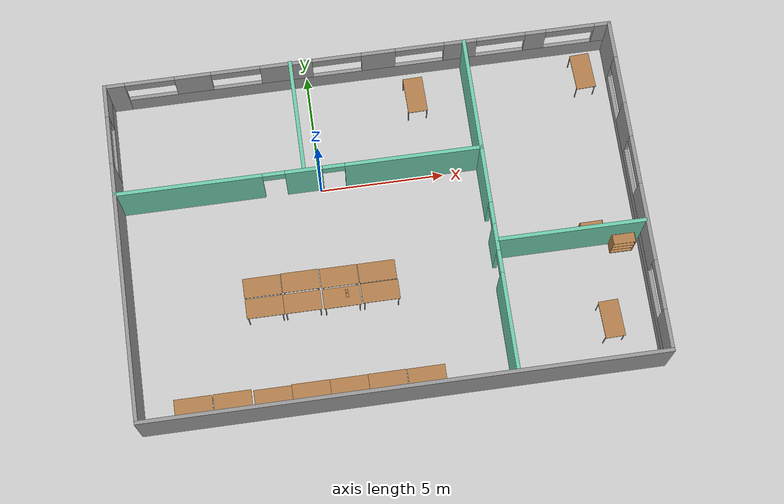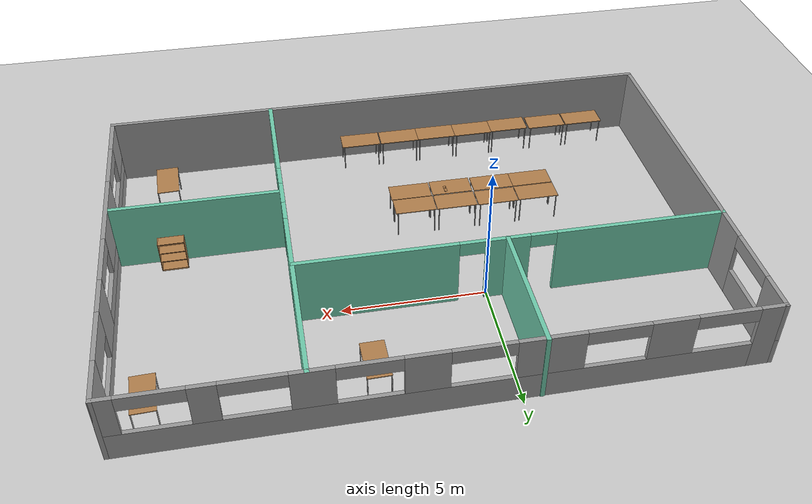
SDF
<sdf version="1.6">
 <world name="default">
  <plugin filename="libcollision_map_creator.so" name="collision_map_creator"/>
  <light name="sun" type="directional">
   <pose>0 0 10 0 -0 0</pose>
   <diffuse>0.8 0.8 0.8 1</diffuse>
   <specular>0.2 0.2 0.2 1</specular>
   <attenuation>
    <range>1000</range>
    <constant>0.9</constant>
    <linear>0.01</linear>
    <quadratic>0.001</quadratic>
   </attenuation>
   <direction>-0.5 0.1 -0.9</direction>
   <spot><inner_angle>0</inner_angle><outer_angle>0</outer_angle><falloff>0</falloff></spot>
  </light>
  <model name="ground_plane">
   <static>1</static>
   <link name="link">
    <collision name="collision">
     <geometry><plane><normal>0 0 1</normal><size>100 100</size></plane></geometry>
     <surface>
      <contact><collide_bitmask>65535</collide_bitmask></contact>
      <friction><ode><mu>100</mu><mu2>50</mu2></ode></friction>
     </surface>
    </collision>
    <visual name="visual">
     <cast_shadows>0</cast_shadows>
     <geometry><plane><normal>0 0 1</normal><size>100 100</size></plane></geometry>
     <material>
      <script><uri>file://media/materials/scripts/gazebo.material</uri><name>Gazebo/Grey</name></script>
     </material>
    </visual>
   </link>
  </model>
  <gravity>0 0 -9.8</gravity>
  <magnetic_field>6e-06 2.3e-05 -4.2e-05</magnetic_field>
  <atmosphere type="adiabatic"/>
  <physics name="default_physics" default="0" type="ode">
   <max_step_size>0.001</max_step_size>
   <real_time_factor>1</real_time_factor>
   <real_time_update_rate>1000</real_time_update_rate>
  </physics>
  <scene><ambient>0.4 0.4 0.4 1</ambient><background>0.7 0.7 0.7 1</background><shadows>1</shadows></scene>
  <spherical_coordinates>
   <surface_model>EARTH_WGS84</surface_model>
   <latitude_deg>0</latitude_deg>
   <longitude_deg>0</longitude_deg>
   <elevation>0</elevation>
   <heading_deg>0</heading_deg>
  </spherical_coordinates>
  <model name="myBuilding">
   <pose>2.16453 -2.14271 0 0 -0 0</pose>
   <link name="Wall_1">
    <pose>0.002237 6.86535 0 0 -0 0</pose>
    <visual name="Wall_1_Visual_0">
     <pose>-9.92957 0 1.25 0 -0 0</pose>
     <geometry><box><size>0.890861 0.15 2.5</size></box></geometry>
     <material>
      <script><uri>file://media/materials/scripts/gazebo.material</uri><name>Gazebo/Grey</name></script>
      <ambient>1 1 1 1</ambient>
     </material>
     <meta><layer>0</layer></meta>
    </visual>
    <collision name="Wall_1_Collision_0">
     <geometry><box><size>0.890861 0.15 2.5</size></box></geometry>
     <pose>-9.92957 0 1.25 0 -0 0</pose>
    </collision>
    <visual name="Wall_1_Visual_1">
     <pose>0.44543 0 0.5 0 -0 0</pose>
     <geometry><box><size>19.8591 0.15 1</size></box></geometry>
     <material>
      <script><uri>file://media/materials/scripts/gazebo.material</uri><name>Gazebo/Grey</name></script>
      <ambient>1 1 1 1</ambient>
     </material>
     <meta><layer>0</layer></meta>
    </visual>
    <collision name="Wall_1_Collision_1">
     <geometry><box><size>19.8591 0.15 1</size></box></geometry>
     <pose>0.44543 0 0.5 0 -0 0</pose>
    </collision>
    <visual name="Wall_1_Visual_2">
     <pose>-6.7459 0 1.75 0 -0 0</pose>
     <geometry><box><size>1.47647 0.15 1.5</size></box></geometry>
     <material>
      <script><uri>file://media/materials/scripts/gazebo.material</uri><name>Gazebo/Grey</name></script>
      <ambient>1 1 1 1</ambient>
     </material>
     <meta><layer>0</layer></meta>
    </visual>
    <collision name="Wall_1_Collision_2">
     <geometry><box><size>1.47647 0.15 1.5</size></box></geometry>
     <pose>-6.7459 0 1.75 0 -0 0</pose>
    </collision>
    <visual name="Wall_1_Visual_3">
     <pose>-2.94421 0 1.75 0 -0 0</pose>
     <geometry><box><size>2.12691 0.15 1.5</size></box></geometry>
     <material>
      <script><uri>file://media/materials/scripts/gazebo.material</uri><name>Gazebo/Grey</name></script>
      <ambient>1 1 1 1</ambient>
     </material>
     <meta><layer>0</layer></meta>
    </visual>
    <collision name="Wall_1_Collision_3">
     <geometry><box><size>2.12691 0.15 1.5</size></box></geometry>
     <pose>-2.94421 0 1.75 0 -0 0</pose>
    </collision>
    <visual name="Wall_1_Visual_4">
     <pose>0.812622 0 1.75 0 -0 0</pose>
     <geometry><box><size>1.38676 0.15 1.5</size></box></geometry>
     <material>
      <script><uri>file://media/materials/scripts/gazebo.material</uri><name>Gazebo/Grey</name></script>
      <ambient>1 1 1 1</ambient>
     </material>
     <meta><layer>0</layer></meta>
    </visual>
    <collision name="Wall_1_Collision_4">
     <geometry><box><size>1.38676 0.15 1.5</size></box></geometry>
     <pose>0.812622 0 1.75 0 -0 0</pose>
    </collision>
    <visual name="Wall_1_Visual_5">
     <pose>4.17695 0 1.75 0 -0 0</pose>
     <geometry><box><size>1.3419 0.15 1.5</size></box></geometry>
     <material>
      <script><uri>file://media/materials/scripts/gazebo.material</uri><name>Gazebo/Grey</name></script>
      <ambient>1 1 1 1</ambient>
     </material>
     <meta><layer>0</layer></meta>
    </visual>
    <collision name="Wall_1_Collision_5">
     <geometry><box><size>1.3419 0.15 1.5</size></box></geometry>
     <pose>4.17695 0 1.75 0 -0 0</pose>
    </collision>
    <visual name="Wall_1_Visual_6">
     <pose>7.27213 0 1.75 0 -0 0</pose>
     <geometry><box><size>0.848465 0.15 1.5</size></box></geometry>
     <material>
      <script><uri>file://media/materials/scripts/gazebo.material</uri><name>Gazebo/Grey</name></script>
      <ambient>1 1 1 1</ambient>
     </material>
     <meta><layer>0</layer></meta>
    </visual>
    <collision name="Wall_1_Collision_6">
     <geometry><box><size>0.848465 0.15 1.5</size></box></geometry>
     <pose>7.27213 0 1.75 0 -0 0</pose>
    </collision>
    <visual name="Wall_1_Visual_7">
     <pose>10.0357 0 1.75 0 -0 0</pose>
     <geometry><box><size>0.678634 0.15 1.5</size></box></geometry>
     <material>
      <script><uri>file://media/materials/scripts/gazebo.material</uri><name>Gazebo/Grey</name></script>
      <ambient>1 1 1 1</ambient>
     </material>
     <meta><layer>0</layer></meta>
    </visual>
    <collision name="Wall_1_Collision_7">
     <geometry><box><size>0.678634 0.15 1.5</size></box></geometry>
     <pose>10.0357 0 1.75 0 -0 0</pose>
    </collision>
    <visual name="Wall_1_Visual_8">
     <pose>-8.48414 0 2.25 0 -0 0</pose>
     <geometry><box><size>2 0.15 0.5</size></box></geometry>
     <material>
      <script><uri>file://media/materials/scripts/gazebo.material</uri><name>Gazebo/Grey</name></script>
      <ambient>1 1 1 1</ambient>
     </material>
     <meta><layer>0</layer></meta>
    </visual>
    <collision name="Wall_1_Collision_8">
     <geometry><box><size>2 0.15 0.5</size></box></geometry>
     <pose>-8.48414 0 2.25 0 -0 0</pose>
    </collision>
    <visual name="Wall_1_Visual_9">
     <pose>-5.00767 0 2.25 0 -0 0</pose>
     <geometry><box><size>2 0.15 0.5</size></box></geometry>
     <material>
      <script><uri>file://media/materials/scripts/gazebo.material</uri><name>Gazebo/Grey</name></script>
      <ambient>1 1 1 1</ambient>
     </material>
     <meta><layer>0</layer></meta>
    </visual>
    <collision name="Wall_1_Collision_9">
     <geometry><box><size>2 0.15 0.5</size></box></geometry>
     <pose>-5.00767 0 2.25 0 -0 0</pose>
    </collision>
    <visual name="Wall_1_Visual_10">
     <pose>-0.880757 0 2.25 0 -0 0</pose>
     <geometry><box><size>2 0.15 0.5</size></box></geometry>
     <material>
      <script><uri>file://media/materials/scripts/gazebo.material</uri><name>Gazebo/Grey</name></script>
      <ambient>1 1 1 1</ambient>
     </material>
     <meta><layer>0</layer></meta>
    </visual>
    <collision name="Wall_1_Collision_10">
     <geometry><box><size>2 0.15 0.5</size></box></geometry>
     <pose>-0.880757 0 2.25 0 -0 0</pose>
    </collision>
    <visual name="Wall_1_Visual_11">
     <pose>2.506 0 2.25 0 -0 0</pose>
     <geometry><box><size>2 0.15 0.5</size></box></geometry>
     <material>
      <script><uri>file://media/materials/scripts/gazebo.material</uri><name>Gazebo/Grey</name></script>
      <ambient>1 1 1 1</ambient>
     </material>
     <meta><layer>0</layer></meta>
    </visual>
    <collision name="Wall_1_Collision_11">
     <geometry><box><size>2 0.15 0.5</size></box></geometry>
     <pose>2.506 0 2.25 0 -0 0</pose>
    </collision>
    <visual name="Wall_1_Visual_12">
     <pose>5.8479 0 2.25 0 -0 0</pose>
     <geometry><box><size>2 0.15 0.5</size></box></geometry>
     <material>
      <script><uri>file://media/materials/scripts/gazebo.material</uri><name>Gazebo/Grey</name></script>
      <ambient>1 1 1 1</ambient>
     </material>
     <meta><layer>0</layer></meta>
    </visual>
    <collision name="Wall_1_Collision_12">
     <geometry><box><size>2 0.15 0.5</size></box></geometry>
     <pose>5.8479 0 2.25 0 -0 0</pose>
    </collision>
    <visual name="Wall_1_Visual_13">
     <pose>8.69637 0 2.25 0 -0 0</pose>
     <geometry><box><size>2 0.15 0.5</size></box></geometry>
     <material>
      <script><uri>file://media/materials/scripts/gazebo.material</uri><name>Gazebo/Grey</name></script>
      <ambient>1 1 1 1</ambient>
     </material>
     <meta><layer>0</layer></meta>
    </visual>
    <collision name="Wall_1_Collision_13">
     <geometry><box><size>2 0.15 0.5</size></box></geometry>
     <pose>8.69637 0 2.25 0 -0 0</pose>
    </collision>
   </link>
   <link name="Wall_12">
    <collision name="Wall_12_Collision">
     <geometry><box><size>4.75 0.15 2.5</size></box></geometry>
     <pose>0 0 1.25 0 -0 0</pose>
    </collision>
    <visual name="Wall_12_Visual">
     <pose>0 0 1.25 0 -0 0</pose>
     <geometry><box><size>4.75 0.15 2.5</size></box></geometry>
     <material>
      <script><uri>file://media/materials/scripts/gazebo.material</uri><name>Gazebo/Grey</name></script>
      <ambient>0.435294 0.796078 0.67451 1</ambient>
     </material>
     <meta><layer>0</layer></meta>
    </visual>
    <pose>4.32498 4.56343 0 0 -0 1.5708</pose>
   </link>
   <link name="Wall_14">
    <pose>4.32498 -2.28657 0 0 0 -1.5708</pose>
    <visual name="Wall_14_Visual_0">
     <pose>-3.42191 0 1.25 0 -0 0</pose>
     <geometry><box><size>2.40618 0.15 2.5</size></box></geometry>
     <material>
      <script><uri>file://media/materials/scripts/gazebo.material</uri><name>Gazebo/Grey</name></script>
      <ambient>0.435294 0.796078 0.67451 1</ambient>
     </material>
     <meta><layer>0</layer></meta>
    </visual>
    <collision name="Wall_14_Collision_0">
     <geometry><box><size>2.40618 0.15 2.5</size></box></geometry>
     <pose>-3.42191 0 1.25 0 -0 0</pose>
    </collision>
    <visual name="Wall_14_Visual_1">
     <pose>-0.770737 0 1.25 0 -0 0</pose>
     <geometry><box><size>1.09617 0.15 2.5</size></box></geometry>
     <material>
      <script><uri>file://media/materials/scripts/gazebo.material</uri><name>Gazebo/Grey</name></script>
      <ambient>0.435294 0.796078 0.67451 1</ambient>
     </material>
     <meta><layer>0</layer></meta>
    </visual>
    <collision name="Wall_14_Collision_1">
     <geometry><box><size>1.09617 0.15 2.5</size></box></geometry>
     <pose>-0.770737 0 1.25 0 -0 0</pose>
    </collision>
    <visual name="Wall_14_Visual_2">
     <pose>2.65117 0 1.25 0 -0 0</pose>
     <geometry><box><size>3.94765 0.15 2.5</size></box></geometry>
     <material>
      <script><uri>file://media/materials/scripts/gazebo.material</uri><name>Gazebo/Grey</name></script>
      <ambient>0.435294 0.796078 0.67451 1</ambient>
     </material>
     <meta><layer>0</layer></meta>
    </visual>
    <collision name="Wall_14_Collision_2">
     <geometry><box><size>3.94765 0.15 2.5</size></box></geometry>
     <pose>2.65117 0 1.25 0 -0 0</pose>
    </collision>
    <visual name="Wall_14_Visual_3">
     <pose>-1.76882 0 2.25 0 -0 0</pose>
     <geometry><box><size>0.9 0.15 0.5</size></box></geometry>
     <material>
      <script><uri>file://media/materials/scripts/gazebo.material</uri><name>Gazebo/Grey</name></script>
      <ambient>0.435294 0.796078 0.67451 1</ambient>
     </material>
     <meta><layer>0</layer></meta>
    </visual>
    <collision name="Wall_14_Collision_3">
     <geometry><box><size>0.9 0.15 0.5</size></box></geometry>
     <pose>-1.76882 0 2.25 0 -0 0</pose>
    </collision>
    <visual name="Wall_14_Visual_4">
     <pose>0.227347 0 2.25 0 -0 0</pose>
     <geometry><box><size>0.9 0.15 0.5</size></box></geometry>
     <material>
      <script><uri>file://media/materials/scripts/gazebo.material</uri><name>Gazebo/Grey</name></script>
      <ambient>0.435294 0.796078 0.67451 1</ambient>
     </material>
     <meta><layer>0</layer></meta>
    </visual>
    <collision name="Wall_14_Collision_4">
     <geometry><box><size>0.9 0.15 0.5</size></box></geometry>
     <pose>0.227347 0 2.25 0 -0 0</pose>
    </collision>
   </link>
   <link name="Wall_16">
    <collision name="Wall_16_Collision">
     <geometry><box><size>6 0.15 2.5</size></box></geometry>
     <pose>0 0 1.25 0 -0 0</pose>
    </collision>
    <visual name="Wall_16_Visual">
     <pose>0 0 1.25 0 -0 0</pose>
     <geometry><box><size>6 0.15 2.5</size></box></geometry>
     <material>
      <script><uri>file://media/materials/scripts/gazebo.material</uri><name>Gazebo/Grey</name></script>
      <ambient>0.435294 0.796078 0.67451 1</ambient>
     </material>
     <meta><layer>0</layer></meta>
    </visual>
    <pose>7.2724 -1.61676 0 0 -0 0</pose>
   </link>
   <link name="Wall_2">
    <pose>10.3022 0.007641 0 0 0 -1.5708</pose>
    <visual name="Wall_2_Visual_0">
     <pose>-6.13719 0 1.25 0 -0 0</pose>
     <geometry><box><size>1.59104 0.15 2.5</size></box></geometry>
     <material>
      <script><uri>file://media/materials/scripts/gazebo.material</uri><name>Gazebo/Grey</name></script>
      <ambient>1 1 1 1</ambient>
     </material>
     <meta><layer>0</layer></meta>
    </visual>
    <collision name="Wall_2_Collision_0">
     <geometry><box><size>1.59104 0.15 2.5</size></box></geometry>
     <pose>-6.13719 0 1.25 0 -0 0</pose>
    </collision>
    <visual name="Wall_2_Visual_1">
     <pose>0.79552 0 0.25 0 -0 0</pose>
     <geometry><box><size>12.2744 0.15 0.5</size></box></geometry>
     <material>
      <script><uri>file://media/materials/scripts/gazebo.material</uri><name>Gazebo/Grey</name></script>
      <ambient>1 1 1 1</ambient>
     </material>
     <meta><layer>0</layer></meta>
    </visual>
    <collision name="Wall_2_Collision_1">
     <geometry><box><size>12.2744 0.15 0.5</size></box></geometry>
     <pose>0.79552 0 0.25 0 -0 0</pose>
    </collision>
    <visual name="Wall_2_Visual_2">
     <pose>-2.61465 0 1.5 0 -0 0</pose>
     <geometry><box><size>1.45404 0.15 2</size></box></geometry>
     <material>
      <script><uri>file://media/materials/scripts/gazebo.material</uri><name>Gazebo/Grey</name></script>
      <ambient>1 1 1 1</ambient>
     </material>
     <meta><layer>0</layer></meta>
    </visual>
    <collision name="Wall_2_Collision_2">
     <geometry><box><size>1.45404 0.15 2</size></box></geometry>
     <pose>-2.61465 0 1.5 0 -0 0</pose>
    </collision>
    <visual name="Wall_2_Visual_3">
     <pose>2.52254 0 0.75 0 -0 0</pose>
     <geometry><box><size>8.82034 0.15 0.5</size></box></geometry>
     <material>
      <script><uri>file://media/materials/scripts/gazebo.material</uri><name>Gazebo/Grey</name></script>
      <ambient>1 1 1 1</ambient>
     </material>
     <meta><layer>0</layer></meta>
    </visual>
    <collision name="Wall_2_Collision_3">
     <geometry><box><size>8.82034 0.15 0.5</size></box></geometry>
     <pose>2.52254 0 0.75 0 -0 0</pose>
    </collision>
    <visual name="Wall_2_Visual_4">
     <pose>1.7029 0 1.75 0 -0 0</pose>
     <geometry><box><size>3.18107 0.15 1.5</size></box></geometry>
     <material>
      <script><uri>file://media/materials/scripts/gazebo.material</uri><name>Gazebo/Grey</name></script>
      <ambient>1 1 1 1</ambient>
     </material>
     <meta><layer>0</layer></meta>
    </visual>
    <collision name="Wall_2_Collision_4">
     <geometry><box><size>3.18107 0.15 1.5</size></box></geometry>
     <pose>1.7029 0 1.75 0 -0 0</pose>
    </collision>
    <visual name="Wall_2_Visual_5">
     <pose>6.11308 0 1.75 0 -0 0</pose>
     <geometry><box><size>1.63928 0.15 1.5</size></box></geometry>
     <material>
      <script><uri>file://media/materials/scripts/gazebo.material</uri><name>Gazebo/Grey</name></script>
      <ambient>1 1 1 1</ambient>
     </material>
     <meta><layer>0</layer></meta>
    </visual>
    <collision name="Wall_2_Collision_5">
     <geometry><box><size>1.63928 0.15 1.5</size></box></geometry>
     <pose>6.11308 0 1.75 0 -0 0</pose>
    </collision>
    <visual name="Wall_2_Visual_6">
     <pose>-4.34167 0 2 0 -0 0</pose>
     <geometry><box><size>2 0.15 1</size></box></geometry>
     <material>
      <script><uri>file://media/materials/scripts/gazebo.material</uri><name>Gazebo/Grey</name></script>
      <ambient>1 1 1 1</ambient>
     </material>
     <meta><layer>0</layer></meta>
    </visual>
    <collision name="Wall_2_Collision_6">
     <geometry><box><size>2 0.15 1</size></box></geometry>
     <pose>-4.34167 0 2 0 -0 0</pose>
    </collision>
    <visual name="Wall_2_Visual_7">
     <pose>-0.88763 0 2.25 0 -0 0</pose>
     <geometry><box><size>2 0.15 0.5</size></box></geometry>
     <material>
      <script><uri>file://media/materials/scripts/gazebo.material</uri><name>Gazebo/Grey</name></script>
      <ambient>1 1 1 1</ambient>
     </material>
     <meta><layer>0</layer></meta>
    </visual>
    <collision name="Wall_2_Collision_7">
     <geometry><box><size>2 0.15 0.5</size></box></geometry>
     <pose>-0.88763 0 2.25 0 -0 0</pose>
    </collision>
    <visual name="Wall_2_Visual_8">
     <pose>4.29344 0 2.25 0 -0 0</pose>
     <geometry><box><size>2 0.15 0.5</size></box></geometry>
     <material>
      <script><uri>file://media/materials/scripts/gazebo.material</uri><name>Gazebo/Grey</name></script>
      <ambient>1 1 1 1</ambient>
     </material>
     <meta><layer>0</layer></meta>
    </visual>
    <collision name="Wall_2_Collision_8">
     <geometry><box><size>2 0.15 0.5</size></box></geometry>
     <pose>4.29344 0 2.25 0 -0 0</pose>
    </collision>
   </link>
   <link name="Wall_3">
    <collision name="Wall_3_Collision">
     <geometry><box><size>20.75 0.15 2.5</size></box></geometry>
     <pose>0 0 1.25 0 -0 0</pose>
    </collision>
    <visual name="Wall_3_Visual">
     <pose>0 0 1.25 0 -0 0</pose>
     <geometry><box><size>20.75 0.15 2.5</size></box></geometry>
     <material>
      <script><uri>file://media/materials/scripts/gazebo.material</uri><name>Gazebo/Grey</name></script>
      <ambient>1 1 1 1</ambient>
     </material>
     <meta><layer>0</layer></meta>
    </visual>
    <pose>0.002237 -6.89493 0 0 -0 3.14159</pose>
   </link>
   <link name="Wall_4">
    <pose>-10.2978 0.007641 0 0 -0 1.5708</pose>
    <visual name="Wall_4_Visual_0">
     <pose>-1.68338 0 1.25 0 -0 0</pose>
     <geometry><box><size>10.4987 0.15 2.5</size></box></geometry>
     <material>
      <script><uri>file://media/materials/scripts/gazebo.material</uri><name>Gazebo/Grey</name></script>
      <ambient>1 1 1 1</ambient>
     </material>
     <meta><layer>0</layer></meta>
    </visual>
    <collision name="Wall_4_Collision_0">
     <geometry><box><size>10.4987 0.15 2.5</size></box></geometry>
     <pose>-1.68338 0 1.25 0 -0 0</pose>
    </collision>
    <visual name="Wall_4_Visual_1">
     <pose>5.24934 0 0.5 0 -0 0</pose>
     <geometry><box><size>3.36675 0.15 1</size></box></geometry>
     <material>
      <script><uri>file://media/materials/scripts/gazebo.material</uri><name>Gazebo/Grey</name></script>
      <ambient>1 1 1 1</ambient>
     </material>
     <meta><layer>0</layer></meta>
    </visual>
    <collision name="Wall_4_Collision_1">
     <geometry><box><size>3.36675 0.15 1</size></box></geometry>
     <pose>5.24934 0 0.5 0 -0 0</pose>
    </collision>
    <visual name="Wall_4_Visual_2">
     <pose>6.24934 0 1.75 0 -0 0</pose>
     <geometry><box><size>1.36675 0.15 1.5</size></box></geometry>
     <material>
      <script><uri>file://media/materials/scripts/gazebo.material</uri><name>Gazebo/Grey</name></script>
      <ambient>1 1 1 1</ambient>
     </material>
     <meta><layer>0</layer></meta>
    </visual>
    <collision name="Wall_4_Collision_2">
     <geometry><box><size>1.36675 0.15 1.5</size></box></geometry>
     <pose>6.24934 0 1.75 0 -0 0</pose>
    </collision>
    <visual name="Wall_4_Visual_3">
     <pose>4.56596 0 2.25 0 -0 0</pose>
     <geometry><box><size>2 0.15 0.5</size></box></geometry>
     <material>
      <script><uri>file://media/materials/scripts/gazebo.material</uri><name>Gazebo/Grey</name></script>
      <ambient>1 1 1 1</ambient>
     </material>
     <meta><layer>0</layer></meta>
    </visual>
    <collision name="Wall_4_Collision_3">
     <geometry><box><size>2 0.15 0.5</size></box></geometry>
     <pose>4.56596 0 2.25 0 -0 0</pose>
    </collision>
   </link>
   <link name="Wall_6">
    <pose>-3.00224 2.26527 0 0 -0 0</pose>
    <visual name="Wall_6_Visual_0">
     <pose>-4.40945 0 1.25 0 -0 0</pose>
     <geometry><box><size>5.93111 0.15 2.5</size></box></geometry>
     <material>
      <script><uri>file://media/materials/scripts/gazebo.material</uri><name>Gazebo/Grey</name></script>
      <ambient>0.435294 0.796078 0.67451 1</ambient>
     </material>
     <meta><layer>0</layer></meta>
    </visual>
    <collision name="Wall_6_Collision_0">
     <geometry><box><size>5.93111 0.15 2.5</size></box></geometry>
     <pose>-4.40945 0 1.25 0 -0 0</pose>
    </collision>
    <visual name="Wall_6_Visual_1">
     <pose>0.20605 0 1.25 0 -0 0</pose>
     <geometry><box><size>1.49989 0.15 2.5</size></box></geometry>
     <material>
      <script><uri>file://media/materials/scripts/gazebo.material</uri><name>Gazebo/Grey</name></script>
      <ambient>0.435294 0.796078 0.67451 1</ambient>
     </material>
     <meta><layer>0</layer></meta>
    </visual>
    <collision name="Wall_6_Collision_1">
     <geometry><box><size>1.49989 0.15 2.5</size></box></geometry>
     <pose>0.20605 0 1.25 0 -0 0</pose>
    </collision>
    <visual name="Wall_6_Visual_2">
     <pose>4.6155 0 1.25 0 -0 0</pose>
     <geometry><box><size>5.51901 0.15 2.5</size></box></geometry>
     <material>
      <script><uri>file://media/materials/scripts/gazebo.material</uri><name>Gazebo/Grey</name></script>
      <ambient>0.435294 0.796078 0.67451 1</ambient>
     </material>
     <meta><layer>0</layer></meta>
    </visual>
    <collision name="Wall_6_Collision_2">
     <geometry><box><size>5.51901 0.15 2.5</size></box></geometry>
     <pose>4.6155 0 1.25 0 -0 0</pose>
    </collision>
    <visual name="Wall_6_Visual_3">
     <pose>-0.993894 0 2.25 0 -0 0</pose>
     <geometry><box><size>0.9 0.15 0.5</size></box></geometry>
     <material>
      <script><uri>file://media/materials/scripts/gazebo.material</uri><name>Gazebo/Grey</name></script>
      <ambient>0.435294 0.796078 0.67451 1</ambient>
     </material>
     <meta><layer>0</layer></meta>
    </visual>
    <collision name="Wall_6_Collision_3">
     <geometry><box><size>0.9 0.15 0.5</size></box></geometry>
     <pose>-0.993894 0 2.25 0 -0 0</pose>
    </collision>
    <visual name="Wall_6_Visual_4">
     <pose>1.40599 0 2.25 0 -0 0</pose>
     <geometry><box><size>0.9 0.15 0.5</size></box></geometry>
     <material>
      <script><uri>file://media/materials/scripts/gazebo.material</uri><name>Gazebo/Grey</name></script>
      <ambient>0.435294 0.796078 0.67451 1</ambient>
     </material>
     <meta><layer>0</layer></meta>
    </visual>
    <collision name="Wall_6_Collision_4">
     <geometry><box><size>0.9 0.15 0.5</size></box></geometry>
     <pose>1.40599 0 2.25 0 -0 0</pose>
    </collision>
   </link>
   <link name="Wall_9">
    <collision name="Wall_9_Collision">
     <geometry><box><size>4.75 0.15 2.5</size></box></geometry>
     <pose>0 0 1.25 0 -0 0</pose>
    </collision>
    <visual name="Wall_9_Visual">
     <pose>0 0 1.25 0 -0 0</pose>
     <geometry><box><size>4.75 0.15 2.5</size></box></geometry>
     <material>
      <script><uri>file://media/materials/scripts/gazebo.material</uri><name>Gazebo/Grey</name></script>
      <ambient>0.435294 0.796078 0.67451 1</ambient>
     </material>
     <meta><layer>0</layer></meta>
    </visual>
    <pose>-2.77747 4.59493 0 0 -0 1.5708</pose>
   </link>
   <static>1</static>
  </model>
  <model name="table">
   <static>1</static>
   <link name="link">
    <collision name="surface">
     <pose>0 0 1 0 -0 0</pose>
     <geometry><box><size>1.5 0.8 0.03</size></box></geometry>
     <surface><friction><ode><mu>0.6</mu><mu2>0.6</mu2></ode></friction></surface>
    </collision>
    <visual name="visual1">
     <pose>0 0 1 0 -0 0</pose>
     <geometry><box><size>1.5 0.8 0.03</size></box></geometry>
     <material>
      <script><uri>file://media/materials/scripts/gazebo.material</uri><name>Gazebo/Wood</name></script>
     </material>
    </visual>
    <collision name="front_left_leg">
     <pose>0.68 0.38 0.5 0 -0 0</pose>
     <geometry><cylinder><radius>0.02</radius><length>1</length></cylinder></geometry>
    </collision>
    <visual name="front_left_leg">
     <pose>0.68 0.38 0.5 0 -0 0</pose>
     <geometry><cylinder><radius>0.02</radius><length>1</length></cylinder></geometry>
     <material>
      <script><uri>file://media/materials/scripts/gazebo.material</uri><name>Gazebo/Grey</name></script>
     </material>
    </visual>
    <collision name="front_right_leg">
     <pose>0.68 -0.38 0.5 0 -0 0</pose>
     <geometry><cylinder><radius>0.02</radius><length>1</length></cylinder></geometry>
    </collision>
    <visual name="front_right_leg">
     <pose>0.68 -0.38 0.5 0 -0 0</pose>
     <geometry><cylinder><radius>0.02</radius><length>1</length></cylinder></geometry>
     <material>
      <script><uri>file://media/materials/scripts/gazebo.material</uri><name>Gazebo/Grey</name></script>
     </material>
    </visual>
    <collision name="back_right_leg">
     <pose>-0.68 -0.38 0.5 0 -0 0</pose>
     <geometry><cylinder><radius>0.02</radius><length>1</length></cylinder></geometry>
    </collision>
    <visual name="back_right_leg">
     <pose>-0.68 -0.38 0.5 0 -0 0</pose>
     <geometry><cylinder><radius>0.02</radius><length>1</length></cylinder></geometry>
     <material>
      <script><uri>file://media/materials/scripts/gazebo.material</uri><name>Gazebo/Grey</name></script>
     </material>
    </visual>
    <collision name="back_left_leg">
     <pose>-0.68 0.38 0.5 0 -0 0</pose>
     <geometry><cylinder><radius>0.02</radius><length>1</length></cylinder></geometry>
    </collision>
    <visual name="back_left_leg">
     <pose>-0.68 0.38 0.5 0 -0 0</pose>
     <geometry><cylinder><radius>0.02</radius><length>1</length></cylinder></geometry>
     <material>
      <script><uri>file://media/materials/scripts/gazebo.material</uri><name>Gazebo/Grey</name></script>
     </material>
    </visual>
   </link>
   <pose>1.73395 -3.9832 0 0 -0 0</pose>
  </model>
  <model name="table_0">
   <static>1</static>
   <link name="link">
    <collision name="surface">
     <pose>0 0 1 0 -0 0</pose>
     <geometry><box><size>1.5 0.8 0.03</size></box></geometry>
     <surface><friction><ode><mu>0.6</mu><mu2>0.6</mu2></ode></friction></surface>
    </collision>
    <visual name="visual1">
     <pose>0 0 1 0 -0 0</pose>
     <geometry><box><size>1.5 0.8 0.03</size></box></geometry>
     <material>
      <script><uri>file://media/materials/scripts/gazebo.material</uri><name>Gazebo/Wood</name></script>
     </material>
    </visual>
    <collision name="front_left_leg">
     <pose>0.68 0.38 0.5 0 -0 0</pose>
     <geometry><cylinder><radius>0.02</radius><length>1</length></cylinder></geometry>
    </collision>
    <visual name="front_left_leg">
     <pose>0.68 0.38 0.5 0 -0 0</pose>
     <geometry><cylinder><radius>0.02</radius><length>1</length></cylinder></geometry>
     <material>
      <script><uri>file://media/materials/scripts/gazebo.material</uri><name>Gazebo/Grey</name></script>
     </material>
    </visual>
    <collision name="front_right_leg">
     <pose>0.68 -0.38 0.5 0 -0 0</pose>
     <geometry><cylinder><radius>0.02</radius><length>1</length></cylinder></geometry>
    </collision>
    <visual name="front_right_leg">
     <pose>0.68 -0.38 0.5 0 -0 0</pose>
     <geometry><cylinder><radius>0.02</radius><length>1</length></cylinder></geometry>
     <material>
      <script><uri>file://media/materials/scripts/gazebo.material</uri><name>Gazebo/Grey</name></script>
     </material>
    </visual>
    <collision name="back_right_leg">
     <pose>-0.68 -0.38 0.5 0 -0 0</pose>
     <geometry><cylinder><radius>0.02</radius><length>1</length></cylinder></geometry>
    </collision>
    <visual name="back_right_leg">
     <pose>-0.68 -0.38 0.5 0 -0 0</pose>
     <geometry><cylinder><radius>0.02</radius><length>1</length></cylinder></geometry>
     <material>
      <script><uri>file://media/materials/scripts/gazebo.material</uri><name>Gazebo/Grey</name></script>
     </material>
    </visual>
    <collision name="back_left_leg">
     <pose>-0.68 0.38 0.5 0 -0 0</pose>
     <geometry><cylinder><radius>0.02</radius><length>1</length></cylinder></geometry>
    </collision>
    <visual name="back_left_leg">
     <pose>-0.68 0.38 0.5 0 -0 0</pose>
     <geometry><cylinder><radius>0.02</radius><length>1</length></cylinder></geometry>
     <material>
      <script><uri>file://media/materials/scripts/gazebo.material</uri><name>Gazebo/Grey</name></script>
     </material>
    </visual>
   </link>
   <pose>1.75648 -4.81123 0 0 -0 0</pose>
  </model>
  <model name="table_1">
   <static>1</static>
   <link name="link">
    <collision name="surface">
     <pose>0 0 1 0 -0 0</pose>
     <geometry><box><size>1.5 0.8 0.03</size></box></geometry>
     <surface><friction><ode><mu>0.6</mu><mu2>0.6</mu2></ode></friction></surface>
    </collision>
    <visual name="visual1">
     <pose>0 0 1 0 -0 0</pose>
     <geometry><box><size>1.5 0.8 0.03</size></box></geometry>
     <material>
      <script><uri>file://media/materials/scripts/gazebo.material</uri><name>Gazebo/Wood</name></script>
     </material>
    </visual>
    <collision name="front_left_leg">
     <pose>0.68 0.38 0.5 0 -0 0</pose>
     <geometry><cylinder><radius>0.02</radius><length>1</length></cylinder></geometry>
    </collision>
    <visual name="front_left_leg">
     <pose>0.68 0.38 0.5 0 -0 0</pose>
     <geometry><cylinder><radius>0.02</radius><length>1</length></cylinder></geometry>
     <material>
      <script><uri>file://media/materials/scripts/gazebo.material</uri><name>Gazebo/Grey</name></script>
     </material>
    </visual>
    <collision name="front_right_leg">
     <pose>0.68 -0.38 0.5 0 -0 0</pose>
     <geometry><cylinder><radius>0.02</radius><length>1</length></cylinder></geometry>
    </collision>
    <visual name="front_right_leg">
     <pose>0.68 -0.38 0.5 0 -0 0</pose>
     <geometry><cylinder><radius>0.02</radius><length>1</length></cylinder></geometry>
     <material>
      <script><uri>file://media/materials/scripts/gazebo.material</uri><name>Gazebo/Grey</name></script>
     </material>
    </visual>
    <collision name="back_right_leg">
     <pose>-0.68 -0.38 0.5 0 -0 0</pose>
     <geometry><cylinder><radius>0.02</radius><length>1</length></cylinder></geometry>
    </collision>
    <visual name="back_right_leg">
     <pose>-0.68 -0.38 0.5 0 -0 0</pose>
     <geometry><cylinder><radius>0.02</radius><length>1</length></cylinder></geometry>
     <material>
      <script><uri>file://media/materials/scripts/gazebo.material</uri><name>Gazebo/Grey</name></script>
     </material>
    </visual>
    <collision name="back_left_leg">
     <pose>-0.68 0.38 0.5 0 -0 0</pose>
     <geometry><cylinder><radius>0.02</radius><length>1</length></cylinder></geometry>
    </collision>
    <visual name="back_left_leg">
     <pose>-0.68 0.38 0.5 0 -0 0</pose>
     <geometry><cylinder><radius>0.02</radius><length>1</length></cylinder></geometry>
     <material>
      <script><uri>file://media/materials/scripts/gazebo.material</uri><name>Gazebo/Grey</name></script>
     </material>
    </visual>
   </link>
   <pose>0.208584 -3.97961 0 0 -0 0</pose>
  </model>
  <model name="table_2">
   <static>1</static>
   <link name="link">
    <collision name="surface">
     <pose>0 0 1 0 -0 0</pose>
     <geometry><box><size>1.5 0.8 0.03</size></box></geometry>
     <surface><friction><ode><mu>0.6</mu><mu2>0.6</mu2></ode></friction></surface>
    </collision>
    <visual name="visual1">
     <pose>0 0 1 0 -0 0</pose>
     <geometry><box><size>1.5 0.8 0.03</size></box></geometry>
     <material>
      <script><uri>file://media/materials/scripts/gazebo.material</uri><name>Gazebo/Wood</name></script>
     </material>
    </visual>
    <collision name="front_left_leg">
     <pose>0.68 0.38 0.5 0 -0 0</pose>
     <geometry><cylinder><radius>0.02</radius><length>1</length></cylinder></geometry>
    </collision>
    <visual name="front_left_leg">
     <pose>0.68 0.38 0.5 0 -0 0</pose>
     <geometry><cylinder><radius>0.02</radius><length>1</length></cylinder></geometry>
     <material>
      <script><uri>file://media/materials/scripts/gazebo.material</uri><name>Gazebo/Grey</name></script>
     </material>
    </visual>
    <collision name="front_right_leg">
     <pose>0.68 -0.38 0.5 0 -0 0</pose>
     <geometry><cylinder><radius>0.02</radius><length>1</length></cylinder></geometry>
    </collision>
    <visual name="front_right_leg">
     <pose>0.68 -0.38 0.5 0 -0 0</pose>
     <geometry><cylinder><radius>0.02</radius><length>1</length></cylinder></geometry>
     <material>
      <script><uri>file://media/materials/scripts/gazebo.material</uri><name>Gazebo/Grey</name></script>
     </material>
    </visual>
    <collision name="back_right_leg">
     <pose>-0.68 -0.38 0.5 0 -0 0</pose>
     <geometry><cylinder><radius>0.02</radius><length>1</length></cylinder></geometry>
    </collision>
    <visual name="back_right_leg">
     <pose>-0.68 -0.38 0.5 0 -0 0</pose>
     <geometry><cylinder><radius>0.02</radius><length>1</length></cylinder></geometry>
     <material>
      <script><uri>file://media/materials/scripts/gazebo.material</uri><name>Gazebo/Grey</name></script>
     </material>
    </visual>
    <collision name="back_left_leg">
     <pose>-0.68 0.38 0.5 0 -0 0</pose>
     <geometry><cylinder><radius>0.02</radius><length>1</length></cylinder></geometry>
    </collision>
    <visual name="back_left_leg">
     <pose>-0.68 0.38 0.5 0 -0 0</pose>
     <geometry><cylinder><radius>0.02</radius><length>1</length></cylinder></geometry>
     <material>
      <script><uri>file://media/materials/scripts/gazebo.material</uri><name>Gazebo/Grey</name></script>
     </material>
    </visual>
   </link>
   <pose>0.212852 -4.83597 0 0 -0 0</pose>
  </model>
  <model name="table_3">
   <static>1</static>
   <link name="link">
    <collision name="surface">
     <pose>0 0 1 0 -0 0</pose>
     <geometry><box><size>1.5 0.8 0.03</size></box></geometry>
     <surface><friction><ode><mu>0.6</mu><mu2>0.6</mu2></ode></friction></surface>
    </collision>
    <visual name="visual1">
     <pose>0 0 1 0 -0 0</pose>
     <geometry><box><size>1.5 0.8 0.03</size></box></geometry>
     <material>
      <script><uri>file://media/materials/scripts/gazebo.material</uri><name>Gazebo/Wood</name></script>
     </material>
    </visual>
    <collision name="front_left_leg">
     <pose>0.68 0.38 0.5 0 -0 0</pose>
     <geometry><cylinder><radius>0.02</radius><length>1</length></cylinder></geometry>
    </collision>
    <visual name="front_left_leg">
     <pose>0.68 0.38 0.5 0 -0 0</pose>
     <geometry><cylinder><radius>0.02</radius><length>1</length></cylinder></geometry>
     <material>
      <script><uri>file://media/materials/scripts/gazebo.material</uri><name>Gazebo/Grey</name></script>
     </material>
    </visual>
    <collision name="front_right_leg">
     <pose>0.68 -0.38 0.5 0 -0 0</pose>
     <geometry><cylinder><radius>0.02</radius><length>1</length></cylinder></geometry>
    </collision>
    <visual name="front_right_leg">
     <pose>0.68 -0.38 0.5 0 -0 0</pose>
     <geometry><cylinder><radius>0.02</radius><length>1</length></cylinder></geometry>
     <material>
      <script><uri>file://media/materials/scripts/gazebo.material</uri><name>Gazebo/Grey</name></script>
     </material>
    </visual>
    <collision name="back_right_leg">
     <pose>-0.68 -0.38 0.5 0 -0 0</pose>
     <geometry><cylinder><radius>0.02</radius><length>1</length></cylinder></geometry>
    </collision>
    <visual name="back_right_leg">
     <pose>-0.68 -0.38 0.5 0 -0 0</pose>
     <geometry><cylinder><radius>0.02</radius><length>1</length></cylinder></geometry>
     <material>
      <script><uri>file://media/materials/scripts/gazebo.material</uri><name>Gazebo/Grey</name></script>
     </material>
    </visual>
    <collision name="back_left_leg">
     <pose>-0.68 0.38 0.5 0 -0 0</pose>
     <geometry><cylinder><radius>0.02</radius><length>1</length></cylinder></geometry>
    </collision>
    <visual name="back_left_leg">
     <pose>-0.68 0.38 0.5 0 -0 0</pose>
     <geometry><cylinder><radius>0.02</radius><length>1</length></cylinder></geometry>
     <material>
      <script><uri>file://media/materials/scripts/gazebo.material</uri><name>Gazebo/Grey</name></script>
     </material>
    </visual>
   </link>
   <pose>3.09695 -8.46773 0 0 -0 0</pose>
  </model>
  <model name="table_4">
   <static>1</static>
   <link name="link">
    <collision name="surface">
     <pose>0 0 1 0 -0 0</pose>
     <geometry><box><size>1.5 0.8 0.03</size></box></geometry>
     <surface><friction><ode><mu>0.6</mu><mu2>0.6</mu2></ode></friction></surface>
    </collision>
    <visual name="visual1">
     <pose>0 0 1 0 -0 0</pose>
     <geometry><box><size>1.5 0.8 0.03</size></box></geometry>
     <material>
      <script><uri>file://media/materials/scripts/gazebo.material</uri><name>Gazebo/Wood</name></script>
     </material>
    </visual>
    <collision name="front_left_leg">
     <pose>0.68 0.38 0.5 0 -0 0</pose>
     <geometry><cylinder><radius>0.02</radius><length>1</length></cylinder></geometry>
    </collision>
    <visual name="front_left_leg">
     <pose>0.68 0.38 0.5 0 -0 0</pose>
     <geometry><cylinder><radius>0.02</radius><length>1</length></cylinder></geometry>
     <material>
      <script><uri>file://media/materials/scripts/gazebo.material</uri><name>Gazebo/Grey</name></script>
     </material>
    </visual>
    <collision name="front_right_leg">
     <pose>0.68 -0.38 0.5 0 -0 0</pose>
     <geometry><cylinder><radius>0.02</radius><length>1</length></cylinder></geometry>
    </collision>
    <visual name="front_right_leg">
     <pose>0.68 -0.38 0.5 0 -0 0</pose>
     <geometry><cylinder><radius>0.02</radius><length>1</length></cylinder></geometry>
     <material>
      <script><uri>file://media/materials/scripts/gazebo.material</uri><name>Gazebo/Grey</name></script>
     </material>
    </visual>
    <collision name="back_right_leg">
     <pose>-0.68 -0.38 0.5 0 -0 0</pose>
     <geometry><cylinder><radius>0.02</radius><length>1</length></cylinder></geometry>
    </collision>
    <visual name="back_right_leg">
     <pose>-0.68 -0.38 0.5 0 -0 0</pose>
     <geometry><cylinder><radius>0.02</radius><length>1</length></cylinder></geometry>
     <material>
      <script><uri>file://media/materials/scripts/gazebo.material</uri><name>Gazebo/Grey</name></script>
     </material>
    </visual>
    <collision name="back_left_leg">
     <pose>-0.68 0.38 0.5 0 -0 0</pose>
     <geometry><cylinder><radius>0.02</radius><length>1</length></cylinder></geometry>
    </collision>
    <visual name="back_left_leg">
     <pose>-0.68 0.38 0.5 0 -0 0</pose>
     <geometry><cylinder><radius>0.02</radius><length>1</length></cylinder></geometry>
     <material>
      <script><uri>file://media/materials/scripts/gazebo.material</uri><name>Gazebo/Grey</name></script>
     </material>
    </visual>
   </link>
   <pose>1.56083 -8.46222 0 0 -0 0</pose>
  </model>
  <model name="table_5">
   <static>1</static>
   <link name="link">
    <collision name="surface">
     <pose>0 0 1 0 -0 0</pose>
     <geometry><box><size>1.5 0.8 0.03</size></box></geometry>
     <surface><friction><ode><mu>0.6</mu><mu2>0.6</mu2></ode></friction></surface>
    </collision>
    <visual name="visual1">
     <pose>0 0 1 0 -0 0</pose>
     <geometry><box><size>1.5 0.8 0.03</size></box></geometry>
     <material>
      <script><uri>file://media/materials/scripts/gazebo.material</uri><name>Gazebo/Wood</name></script>
     </material>
    </visual>
    <collision name="front_left_leg">
     <pose>0.68 0.38 0.5 0 -0 0</pose>
     <geometry><cylinder><radius>0.02</radius><length>1</length></cylinder></geometry>
    </collision>
    <visual name="front_left_leg">
     <pose>0.68 0.38 0.5 0 -0 0</pose>
     <geometry><cylinder><radius>0.02</radius><length>1</length></cylinder></geometry>
     <material>
      <script><uri>file://media/materials/scripts/gazebo.material</uri><name>Gazebo/Grey</name></script>
     </material>
    </visual>
    <collision name="front_right_leg">
     <pose>0.68 -0.38 0.5 0 -0 0</pose>
     <geometry><cylinder><radius>0.02</radius><length>1</length></cylinder></geometry>
    </collision>
    <visual name="front_right_leg">
     <pose>0.68 -0.38 0.5 0 -0 0</pose>
     <geometry><cylinder><radius>0.02</radius><length>1</length></cylinder></geometry>
     <material>
      <script><uri>file://media/materials/scripts/gazebo.material</uri><name>Gazebo/Grey</name></script>
     </material>
    </visual>
    <collision name="back_right_leg">
     <pose>-0.68 -0.38 0.5 0 -0 0</pose>
     <geometry><cylinder><radius>0.02</radius><length>1</length></cylinder></geometry>
    </collision>
    <visual name="back_right_leg">
     <pose>-0.68 -0.38 0.5 0 -0 0</pose>
     <geometry><cylinder><radius>0.02</radius><length>1</length></cylinder></geometry>
     <material>
      <script><uri>file://media/materials/scripts/gazebo.material</uri><name>Gazebo/Grey</name></script>
     </material>
    </visual>
    <collision name="back_left_leg">
     <pose>-0.68 0.38 0.5 0 -0 0</pose>
     <geometry><cylinder><radius>0.02</radius><length>1</length></cylinder></geometry>
    </collision>
    <visual name="back_left_leg">
     <pose>-0.68 0.38 0.5 0 -0 0</pose>
     <geometry><cylinder><radius>0.02</radius><length>1</length></cylinder></geometry>
     <material>
      <script><uri>file://media/materials/scripts/gazebo.material</uri><name>Gazebo/Grey</name></script>
     </material>
    </visual>
   </link>
   <pose>0.063502 -8.46912 0 0 -0 0</pose>
  </model>
  <model name="table_6">
   <static>1</static>
   <link name="link">
    <collision name="surface">
     <pose>0 0 1 0 -0 0</pose>
     <geometry><box><size>1.5 0.8 0.03</size></box></geometry>
     <surface><friction><ode><mu>0.6</mu><mu2>0.6</mu2></ode></friction></surface>
    </collision>
    <visual name="visual1">
     <pose>0 0 1 0 -0 0</pose>
     <geometry><box><size>1.5 0.8 0.03</size></box></geometry>
     <material>
      <script><uri>file://media/materials/scripts/gazebo.material</uri><name>Gazebo/Wood</name></script>
     </material>
    </visual>
    <collision name="front_left_leg">
     <pose>0.68 0.38 0.5 0 -0 0</pose>
     <geometry><cylinder><radius>0.02</radius><length>1</length></cylinder></geometry>
    </collision>
    <visual name="front_left_leg">
     <pose>0.68 0.38 0.5 0 -0 0</pose>
     <geometry><cylinder><radius>0.02</radius><length>1</length></cylinder></geometry>
     <material>
      <script><uri>file://media/materials/scripts/gazebo.material</uri><name>Gazebo/Grey</name></script>
     </material>
    </visual>
    <collision name="front_right_leg">
     <pose>0.68 -0.38 0.5 0 -0 0</pose>
     <geometry><cylinder><radius>0.02</radius><length>1</length></cylinder></geometry>
    </collision>
    <visual name="front_right_leg">
     <pose>0.68 -0.38 0.5 0 -0 0</pose>
     <geometry><cylinder><radius>0.02</radius><length>1</length></cylinder></geometry>
     <material>
      <script><uri>file://media/materials/scripts/gazebo.material</uri><name>Gazebo/Grey</name></script>
     </material>
    </visual>
    <collision name="back_right_leg">
     <pose>-0.68 -0.38 0.5 0 -0 0</pose>
     <geometry><cylinder><radius>0.02</radius><length>1</length></cylinder></geometry>
    </collision>
    <visual name="back_right_leg">
     <pose>-0.68 -0.38 0.5 0 -0 0</pose>
     <geometry><cylinder><radius>0.02</radius><length>1</length></cylinder></geometry>
     <material>
      <script><uri>file://media/materials/scripts/gazebo.material</uri><name>Gazebo/Grey</name></script>
     </material>
    </visual>
    <collision name="back_left_leg">
     <pose>-0.68 0.38 0.5 0 -0 0</pose>
     <geometry><cylinder><radius>0.02</radius><length>1</length></cylinder></geometry>
    </collision>
    <visual name="back_left_leg">
     <pose>-0.68 0.38 0.5 0 -0 0</pose>
     <geometry><cylinder><radius>0.02</radius><length>1</length></cylinder></geometry>
     <material>
      <script><uri>file://media/materials/scripts/gazebo.material</uri><name>Gazebo/Grey</name></script>
     </material>
    </visual>
   </link>
   <pose>-1.4363 -8.46318 0 0 -0 0</pose>
  </model>
  <model name="table_7">
   <static>1</static>
   <link name="link">
    <collision name="surface">
     <pose>0 0 1 0 -0 0</pose>
     <geometry><box><size>1.5 0.8 0.03</size></box></geometry>
     <surface><friction><ode><mu>0.6</mu><mu2>0.6</mu2></ode></friction></surface>
    </collision>
    <visual name="visual1">
     <pose>0 0 1 0 -0 0</pose>
     <geometry><box><size>1.5 0.8 0.03</size></box></geometry>
     <material>
      <script><uri>file://media/materials/scripts/gazebo.material</uri><name>Gazebo/Wood</name></script>
     </material>
    </visual>
    <collision name="front_left_leg">
     <pose>0.68 0.38 0.5 0 -0 0</pose>
     <geometry><cylinder><radius>0.02</radius><length>1</length></cylinder></geometry>
    </collision>
    <visual name="front_left_leg">
     <pose>0.68 0.38 0.5 0 -0 0</pose>
     <geometry><cylinder><radius>0.02</radius><length>1</length></cylinder></geometry>
     <material>
      <script><uri>file://media/materials/scripts/gazebo.material</uri><name>Gazebo/Grey</name></script>
     </material>
    </visual>
    <collision name="front_right_leg">
     <pose>0.68 -0.38 0.5 0 -0 0</pose>
     <geometry><cylinder><radius>0.02</radius><length>1</length></cylinder></geometry>
    </collision>
    <visual name="front_right_leg">
     <pose>0.68 -0.38 0.5 0 -0 0</pose>
     <geometry><cylinder><radius>0.02</radius><length>1</length></cylinder></geometry>
     <material>
      <script><uri>file://media/materials/scripts/gazebo.material</uri><name>Gazebo/Grey</name></script>
     </material>
    </visual>
    <collision name="back_right_leg">
     <pose>-0.68 -0.38 0.5 0 -0 0</pose>
     <geometry><cylinder><radius>0.02</radius><length>1</length></cylinder></geometry>
    </collision>
    <visual name="back_right_leg">
     <pose>-0.68 -0.38 0.5 0 -0 0</pose>
     <geometry><cylinder><radius>0.02</radius><length>1</length></cylinder></geometry>
     <material>
      <script><uri>file://media/materials/scripts/gazebo.material</uri><name>Gazebo/Grey</name></script>
     </material>
    </visual>
    <collision name="back_left_leg">
     <pose>-0.68 0.38 0.5 0 -0 0</pose>
     <geometry><cylinder><radius>0.02</radius><length>1</length></cylinder></geometry>
    </collision>
    <visual name="back_left_leg">
     <pose>-0.68 0.38 0.5 0 -0 0</pose>
     <geometry><cylinder><radius>0.02</radius><length>1</length></cylinder></geometry>
     <material>
      <script><uri>file://media/materials/scripts/gazebo.material</uri><name>Gazebo/Grey</name></script>
     </material>
    </visual>
   </link>
   <pose>-2.92424 -8.49258 0 0 -0 0</pose>
  </model>
  <model name="table_8">
   <static>1</static>
   <link name="link">
    <collision name="surface">
     <pose>0 0 1 0 -0 0</pose>
     <geometry><box><size>1.5 0.8 0.03</size></box></geometry>
     <surface><friction><ode><mu>0.6</mu><mu2>0.6</mu2></ode></friction></surface>
    </collision>
    <visual name="visual1">
     <pose>0 0 1 0 -0 0</pose>
     <geometry><box><size>1.5 0.8 0.03</size></box></geometry>
     <material>
      <script><uri>file://media/materials/scripts/gazebo.material</uri><name>Gazebo/Wood</name></script>
     </material>
    </visual>
    <collision name="front_left_leg">
     <pose>0.68 0.38 0.5 0 -0 0</pose>
     <geometry><cylinder><radius>0.02</radius><length>1</length></cylinder></geometry>
    </collision>
    <visual name="front_left_leg">
     <pose>0.68 0.38 0.5 0 -0 0</pose>
     <geometry><cylinder><radius>0.02</radius><length>1</length></cylinder></geometry>
     <material>
      <script><uri>file://media/materials/scripts/gazebo.material</uri><name>Gazebo/Grey</name></script>
     </material>
    </visual>
    <collision name="front_right_leg">
     <pose>0.68 -0.38 0.5 0 -0 0</pose>
     <geometry><cylinder><radius>0.02</radius><length>1</length></cylinder></geometry>
    </collision>
    <visual name="front_right_leg">
     <pose>0.68 -0.38 0.5 0 -0 0</pose>
     <geometry><cylinder><radius>0.02</radius><length>1</length></cylinder></geometry>
     <material>
      <script><uri>file://media/materials/scripts/gazebo.material</uri><name>Gazebo/Grey</name></script>
     </material>
    </visual>
    <collision name="back_right_leg">
     <pose>-0.68 -0.38 0.5 0 -0 0</pose>
     <geometry><cylinder><radius>0.02</radius><length>1</length></cylinder></geometry>
    </collision>
    <visual name="back_right_leg">
     <pose>-0.68 -0.38 0.5 0 -0 0</pose>
     <geometry><cylinder><radius>0.02</radius><length>1</length></cylinder></geometry>
     <material>
      <script><uri>file://media/materials/scripts/gazebo.material</uri><name>Gazebo/Grey</name></script>
     </material>
    </visual>
    <collision name="back_left_leg">
     <pose>-0.68 0.38 0.5 0 -0 0</pose>
     <geometry><cylinder><radius>0.02</radius><length>1</length></cylinder></geometry>
    </collision>
    <visual name="back_left_leg">
     <pose>-0.68 0.38 0.5 0 -0 0</pose>
     <geometry><cylinder><radius>0.02</radius><length>1</length></cylinder></geometry>
     <material>
      <script><uri>file://media/materials/scripts/gazebo.material</uri><name>Gazebo/Grey</name></script>
     </material>
    </visual>
   </link>
   <pose>-4.50753 -8.4409 0 0 -0 0</pose>
  </model>
  <model name="table_9">
   <static>1</static>
   <link name="link">
    <collision name="surface">
     <pose>0 0 1 0 -0 0</pose>
     <geometry><box><size>1.5 0.8 0.03</size></box></geometry>
     <surface><friction><ode><mu>0.6</mu><mu2>0.6</mu2></ode></friction></surface>
    </collision>
    <visual name="visual1">
     <pose>0 0 1 0 -0 0</pose>
     <geometry><box><size>1.5 0.8 0.03</size></box></geometry>
     <material>
      <script><uri>file://media/materials/scripts/gazebo.material</uri><name>Gazebo/Wood</name></script>
     </material>
    </visual>
    <collision name="front_left_leg">
     <pose>0.68 0.38 0.5 0 -0 0</pose>
     <geometry><cylinder><radius>0.02</radius><length>1</length></cylinder></geometry>
    </collision>
    <visual name="front_left_leg">
     <pose>0.68 0.38 0.5 0 -0 0</pose>
     <geometry><cylinder><radius>0.02</radius><length>1</length></cylinder></geometry>
     <material>
      <script><uri>file://media/materials/scripts/gazebo.material</uri><name>Gazebo/Grey</name></script>
     </material>
    </visual>
    <collision name="front_right_leg">
     <pose>0.68 -0.38 0.5 0 -0 0</pose>
     <geometry><cylinder><radius>0.02</radius><length>1</length></cylinder></geometry>
    </collision>
    <visual name="front_right_leg">
     <pose>0.68 -0.38 0.5 0 -0 0</pose>
     <geometry><cylinder><radius>0.02</radius><length>1</length></cylinder></geometry>
     <material>
      <script><uri>file://media/materials/scripts/gazebo.material</uri><name>Gazebo/Grey</name></script>
     </material>
    </visual>
    <collision name="back_right_leg">
     <pose>-0.68 -0.38 0.5 0 -0 0</pose>
     <geometry><cylinder><radius>0.02</radius><length>1</length></cylinder></geometry>
    </collision>
    <visual name="back_right_leg">
     <pose>-0.68 -0.38 0.5 0 -0 0</pose>
     <geometry><cylinder><radius>0.02</radius><length>1</length></cylinder></geometry>
     <material>
      <script><uri>file://media/materials/scripts/gazebo.material</uri><name>Gazebo/Grey</name></script>
     </material>
    </visual>
    <collision name="back_left_leg">
     <pose>-0.68 0.38 0.5 0 -0 0</pose>
     <geometry><cylinder><radius>0.02</radius><length>1</length></cylinder></geometry>
    </collision>
    <visual name="back_left_leg">
     <pose>-0.68 0.38 0.5 0 -0 0</pose>
     <geometry><cylinder><radius>0.02</radius><length>1</length></cylinder></geometry>
     <material>
      <script><uri>file://media/materials/scripts/gazebo.material</uri><name>Gazebo/Grey</name></script>
     </material>
    </visual>
   </link>
   <pose>-1.35243 -4.82062 0 0 -0 0</pose>
  </model>
  <model name="table_10">
   <static>1</static>
   <link name="link">
    <collision name="surface">
     <pose>0 0 1 0 -0 0</pose>
     <geometry><box><size>1.5 0.8 0.03</size></box></geometry>
     <surface><friction><ode><mu>0.6</mu><mu2>0.6</mu2></ode></friction></surface>
    </collision>
    <visual name="visual1">
     <pose>0 0 1 0 -0 0</pose>
     <geometry><box><size>1.5 0.8 0.03</size></box></geometry>
     <material>
      <script><uri>file://media/materials/scripts/gazebo.material</uri><name>Gazebo/Wood</name></script>
     </material>
    </visual>
    <collision name="front_left_leg">
     <pose>0.68 0.38 0.5 0 -0 0</pose>
     <geometry><cylinder><radius>0.02</radius><length>1</length></cylinder></geometry>
    </collision>
    <visual name="front_left_leg">
     <pose>0.68 0.38 0.5 0 -0 0</pose>
     <geometry><cylinder><radius>0.02</radius><length>1</length></cylinder></geometry>
     <material>
      <script><uri>file://media/materials/scripts/gazebo.material</uri><name>Gazebo/Grey</name></script>
     </material>
    </visual>
    <collision name="front_right_leg">
     <pose>0.68 -0.38 0.5 0 -0 0</pose>
     <geometry><cylinder><radius>0.02</radius><length>1</length></cylinder></geometry>
    </collision>
    <visual name="front_right_leg">
     <pose>0.68 -0.38 0.5 0 -0 0</pose>
     <geometry><cylinder><radius>0.02</radius><length>1</length></cylinder></geometry>
     <material>
      <script><uri>file://media/materials/scripts/gazebo.material</uri><name>Gazebo/Grey</name></script>
     </material>
    </visual>
    <collision name="back_right_leg">
     <pose>-0.68 -0.38 0.5 0 -0 0</pose>
     <geometry><cylinder><radius>0.02</radius><length>1</length></cylinder></geometry>
    </collision>
    <visual name="back_right_leg">
     <pose>-0.68 -0.38 0.5 0 -0 0</pose>
     <geometry><cylinder><radius>0.02</radius><length>1</length></cylinder></geometry>
     <material>
      <script><uri>file://media/materials/scripts/gazebo.material</uri><name>Gazebo/Grey</name></script>
     </material>
    </visual>
    <collision name="back_left_leg">
     <pose>-0.68 0.38 0.5 0 -0 0</pose>
     <geometry><cylinder><radius>0.02</radius><length>1</length></cylinder></geometry>
    </collision>
    <visual name="back_left_leg">
     <pose>-0.68 0.38 0.5 0 -0 0</pose>
     <geometry><cylinder><radius>0.02</radius><length>1</length></cylinder></geometry>
     <material>
      <script><uri>file://media/materials/scripts/gazebo.material</uri><name>Gazebo/Grey</name></script>
     </material>
    </visual>
   </link>
   <pose>-1.33048 -3.9602 0 0 -0 0</pose>
  </model>
  <model name="table_11">
   <static>1</static>
   <link name="link">
    <collision name="surface">
     <pose>0 0 1 0 -0 0</pose>
     <geometry><box><size>1.5 0.8 0.03</size></box></geometry>
     <surface><friction><ode><mu>0.6</mu><mu2>0.6</mu2></ode></friction></surface>
    </collision>
    <visual name="visual1">
     <pose>0 0 1 0 -0 0</pose>
     <geometry><box><size>1.5 0.8 0.03</size></box></geometry>
     <material>
      <script><uri>file://media/materials/scripts/gazebo.material</uri><name>Gazebo/Wood</name></script>
     </material>
    </visual>
    <collision name="front_left_leg">
     <pose>0.68 0.38 0.5 0 -0 0</pose>
     <geometry><cylinder><radius>0.02</radius><length>1</length></cylinder></geometry>
    </collision>
    <visual name="front_left_leg">
     <pose>0.68 0.38 0.5 0 -0 0</pose>
     <geometry><cylinder><radius>0.02</radius><length>1</length></cylinder></geometry>
     <material>
      <script><uri>file://media/materials/scripts/gazebo.material</uri><name>Gazebo/Grey</name></script>
     </material>
    </visual>
    <collision name="front_right_leg">
     <pose>0.68 -0.38 0.5 0 -0 0</pose>
     <geometry><cylinder><radius>0.02</radius><length>1</length></cylinder></geometry>
    </collision>
    <visual name="front_right_leg">
     <pose>0.68 -0.38 0.5 0 -0 0</pose>
     <geometry><cylinder><radius>0.02</radius><length>1</length></cylinder></geometry>
     <material>
      <script><uri>file://media/materials/scripts/gazebo.material</uri><name>Gazebo/Grey</name></script>
     </material>
    </visual>
    <collision name="back_right_leg">
     <pose>-0.68 -0.38 0.5 0 -0 0</pose>
     <geometry><cylinder><radius>0.02</radius><length>1</length></cylinder></geometry>
    </collision>
    <visual name="back_right_leg">
     <pose>-0.68 -0.38 0.5 0 -0 0</pose>
     <geometry><cylinder><radius>0.02</radius><length>1</length></cylinder></geometry>
     <material>
      <script><uri>file://media/materials/scripts/gazebo.material</uri><name>Gazebo/Grey</name></script>
     </material>
    </visual>
    <collision name="back_left_leg">
     <pose>-0.68 0.38 0.5 0 -0 0</pose>
     <geometry><cylinder><radius>0.02</radius><length>1</length></cylinder></geometry>
    </collision>
    <visual name="back_left_leg">
     <pose>-0.68 0.38 0.5 0 -0 0</pose>
     <geometry><cylinder><radius>0.02</radius><length>1</length></cylinder></geometry>
     <material>
      <script><uri>file://media/materials/scripts/gazebo.material</uri><name>Gazebo/Grey</name></script>
     </material>
    </visual>
   </link>
   <pose>-2.8522 -4.82056 0 0 -0 0</pose>
  </model>
  <model name="table_12">
   <static>1</static>
   <link name="link">
    <collision name="surface">
     <pose>0 0 1 0 -0 0</pose>
     <geometry><box><size>1.5 0.8 0.03</size></box></geometry>
     <surface><friction><ode><mu>0.6</mu><mu2>0.6</mu2></ode></friction></surface>
    </collision>
    <visual name="visual1">
     <pose>0 0 1 0 -0 0</pose>
     <geometry><box><size>1.5 0.8 0.03</size></box></geometry>
     <material>
      <script><uri>file://media/materials/scripts/gazebo.material</uri><name>Gazebo/Wood</name></script>
     </material>
    </visual>
    <collision name="front_left_leg">
     <pose>0.68 0.38 0.5 0 -0 0</pose>
     <geometry><cylinder><radius>0.02</radius><length>1</length></cylinder></geometry>
    </collision>
    <visual name="front_left_leg">
     <pose>0.68 0.38 0.5 0 -0 0</pose>
     <geometry><cylinder><radius>0.02</radius><length>1</length></cylinder></geometry>
     <material>
      <script><uri>file://media/materials/scripts/gazebo.material</uri><name>Gazebo/Grey</name></script>
     </material>
    </visual>
    <collision name="front_right_leg">
     <pose>0.68 -0.38 0.5 0 -0 0</pose>
     <geometry><cylinder><radius>0.02</radius><length>1</length></cylinder></geometry>
    </collision>
    <visual name="front_right_leg">
     <pose>0.68 -0.38 0.5 0 -0 0</pose>
     <geometry><cylinder><radius>0.02</radius><length>1</length></cylinder></geometry>
     <material>
      <script><uri>file://media/materials/scripts/gazebo.material</uri><name>Gazebo/Grey</name></script>
     </material>
    </visual>
    <collision name="back_right_leg">
     <pose>-0.68 -0.38 0.5 0 -0 0</pose>
     <geometry><cylinder><radius>0.02</radius><length>1</length></cylinder></geometry>
    </collision>
    <visual name="back_right_leg">
     <pose>-0.68 -0.38 0.5 0 -0 0</pose>
     <geometry><cylinder><radius>0.02</radius><length>1</length></cylinder></geometry>
     <material>
      <script><uri>file://media/materials/scripts/gazebo.material</uri><name>Gazebo/Grey</name></script>
     </material>
    </visual>
    <collision name="back_left_leg">
     <pose>-0.68 0.38 0.5 0 -0 0</pose>
     <geometry><cylinder><radius>0.02</radius><length>1</length></cylinder></geometry>
    </collision>
    <visual name="back_left_leg">
     <pose>-0.68 0.38 0.5 0 -0 0</pose>
     <geometry><cylinder><radius>0.02</radius><length>1</length></cylinder></geometry>
     <material>
      <script><uri>file://media/materials/scripts/gazebo.material</uri><name>Gazebo/Grey</name></script>
     </material>
    </visual>
   </link>
   <pose>-2.85737 -3.97832 0 0 -0 0</pose>
  </model>
  <model name="table_13">
   <static>1</static>
   <link name="link">
    <collision name="surface">
     <pose>0 0 1 0 -0 0</pose>
     <geometry><box><size>1.5 0.8 0.03</size></box></geometry>
     <surface><friction><ode><mu>0.6</mu><mu2>0.6</mu2></ode></friction></surface>
    </collision>
    <visual name="visual1">
     <pose>0 0 1 0 -0 0</pose>
     <geometry><box><size>1.5 0.8 0.03</size></box></geometry>
     <material>
      <script><uri>file://media/materials/scripts/gazebo.material</uri><name>Gazebo/Wood</name></script>
     </material>
    </visual>
    <collision name="front_left_leg">
     <pose>0.68 0.38 0.5 0 -0 0</pose>
     <geometry><cylinder><radius>0.02</radius><length>1</length></cylinder></geometry>
    </collision>
    <visual name="front_left_leg">
     <pose>0.68 0.38 0.5 0 -0 0</pose>
     <geometry><cylinder><radius>0.02</radius><length>1</length></cylinder></geometry>
     <material>
      <script><uri>file://media/materials/scripts/gazebo.material</uri><name>Gazebo/Grey</name></script>
     </material>
    </visual>
    <collision name="front_right_leg">
     <pose>0.68 -0.38 0.5 0 -0 0</pose>
     <geometry><cylinder><radius>0.02</radius><length>1</length></cylinder></geometry>
    </collision>
    <visual name="front_right_leg">
     <pose>0.68 -0.38 0.5 0 -0 0</pose>
     <geometry><cylinder><radius>0.02</radius><length>1</length></cylinder></geometry>
     <material>
      <script><uri>file://media/materials/scripts/gazebo.material</uri><name>Gazebo/Grey</name></script>
     </material>
    </visual>
    <collision name="back_right_leg">
     <pose>-0.68 -0.38 0.5 0 -0 0</pose>
     <geometry><cylinder><radius>0.02</radius><length>1</length></cylinder></geometry>
    </collision>
    <visual name="back_right_leg">
     <pose>-0.68 -0.38 0.5 0 -0 0</pose>
     <geometry><cylinder><radius>0.02</radius><length>1</length></cylinder></geometry>
     <material>
      <script><uri>file://media/materials/scripts/gazebo.material</uri><name>Gazebo/Grey</name></script>
     </material>
    </visual>
    <collision name="back_left_leg">
     <pose>-0.68 0.38 0.5 0 -0 0</pose>
     <geometry><cylinder><radius>0.02</radius><length>1</length></cylinder></geometry>
    </collision>
    <visual name="back_left_leg">
     <pose>-0.68 0.38 0.5 0 -0 0</pose>
     <geometry><cylinder><radius>0.02</radius><length>1</length></cylinder></geometry>
     <material>
      <script><uri>file://media/materials/scripts/gazebo.material</uri><name>Gazebo/Grey</name></script>
     </material>
    </visual>
   </link>
   <pose>-6.04338 -8.44713 0 0 -0 0</pose>
  </model>
  <model name="table_14">
   <static>1</static>
   <link name="link">
    <collision name="surface">
     <pose>0 0 1 0 -0 0</pose>
     <geometry><box><size>1.5 0.8 0.03</size></box></geometry>
     <surface><friction><ode><mu>0.6</mu><mu2>0.6</mu2></ode></friction></surface>
    </collision>
    <visual name="visual1">
     <pose>0 0 1 0 -0 0</pose>
     <geometry><box><size>1.5 0.8 0.03</size></box></geometry>
     <material>
      <script><uri>file://media/materials/scripts/gazebo.material</uri><name>Gazebo/Wood</name></script>
     </material>
    </visual>
    <collision name="front_left_leg">
     <pose>0.68 0.38 0.5 0 -0 0</pose>
     <geometry><cylinder><radius>0.02</radius><length>1</length></cylinder></geometry>
    </collision>
    <visual name="front_left_leg">
     <pose>0.68 0.38 0.5 0 -0 0</pose>
     <geometry><cylinder><radius>0.02</radius><length>1</length></cylinder></geometry>
     <material>
      <script><uri>file://media/materials/scripts/gazebo.material</uri><name>Gazebo/Grey</name></script>
     </material>
    </visual>
    <collision name="front_right_leg">
     <pose>0.68 -0.38 0.5 0 -0 0</pose>
     <geometry><cylinder><radius>0.02</radius><length>1</length></cylinder></geometry>
    </collision>
    <visual name="front_right_leg">
     <pose>0.68 -0.38 0.5 0 -0 0</pose>
     <geometry><cylinder><radius>0.02</radius><length>1</length></cylinder></geometry>
     <material>
      <script><uri>file://media/materials/scripts/gazebo.material</uri><name>Gazebo/Grey</name></script>
     </material>
    </visual>
    <collision name="back_right_leg">
     <pose>-0.68 -0.38 0.5 0 -0 0</pose>
     <geometry><cylinder><radius>0.02</radius><length>1</length></cylinder></geometry>
    </collision>
    <visual name="back_right_leg">
     <pose>-0.68 -0.38 0.5 0 -0 0</pose>
     <geometry><cylinder><radius>0.02</radius><length>1</length></cylinder></geometry>
     <material>
      <script><uri>file://media/materials/scripts/gazebo.material</uri><name>Gazebo/Grey</name></script>
     </material>
    </visual>
    <collision name="back_left_leg">
     <pose>-0.68 0.38 0.5 0 -0 0</pose>
     <geometry><cylinder><radius>0.02</radius><length>1</length></cylinder></geometry>
    </collision>
    <visual name="back_left_leg">
     <pose>-0.68 0.38 0.5 0 -0 0</pose>
     <geometry><cylinder><radius>0.02</radius><length>1</length></cylinder></geometry>
     <material>
      <script><uri>file://media/materials/scripts/gazebo.material</uri><name>Gazebo/Grey</name></script>
     </material>
    </visual>
   </link>
   <pose>10.6267 -7.17024 0 0 -0 1.60543</pose>
  </model>
  <model name="table_15">
   <static>1</static>
   <link name="link">
    <collision name="surface">
     <pose>0 0 1 0 -0 0</pose>
     <geometry><box><size>1.5 0.8 0.03</size></box></geometry>
     <surface><friction><ode><mu>0.6</mu><mu2>0.6</mu2></ode></friction></surface>
    </collision>
    <visual name="visual1">
     <pose>0 0 1 0 -0 0</pose>
     <geometry><box><size>1.5 0.8 0.03</size></box></geometry>
     <material>
      <script><uri>file://media/materials/scripts/gazebo.material</uri><name>Gazebo/Wood</name></script>
     </material>
    </visual>
    <collision name="front_left_leg">
     <pose>0.68 0.38 0.5 0 -0 0</pose>
     <geometry><cylinder><radius>0.02</radius><length>1</length></cylinder></geometry>
    </collision>
    <visual name="front_left_leg">
     <pose>0.68 0.38 0.5 0 -0 0</pose>
     <geometry><cylinder><radius>0.02</radius><length>1</length></cylinder></geometry>
     <material>
      <script><uri>file://media/materials/scripts/gazebo.material</uri><name>Gazebo/Grey</name></script>
     </material>
    </visual>
    <collision name="front_right_leg">
     <pose>0.68 -0.38 0.5 0 -0 0</pose>
     <geometry><cylinder><radius>0.02</radius><length>1</length></cylinder></geometry>
    </collision>
    <visual name="front_right_leg">
     <pose>0.68 -0.38 0.5 0 -0 0</pose>
     <geometry><cylinder><radius>0.02</radius><length>1</length></cylinder></geometry>
     <material>
      <script><uri>file://media/materials/scripts/gazebo.material</uri><name>Gazebo/Grey</name></script>
     </material>
    </visual>
    <collision name="back_right_leg">
     <pose>-0.68 -0.38 0.5 0 -0 0</pose>
     <geometry><cylinder><radius>0.02</radius><length>1</length></cylinder></geometry>
    </collision>
    <visual name="back_right_leg">
     <pose>-0.68 -0.38 0.5 0 -0 0</pose>
     <geometry><cylinder><radius>0.02</radius><length>1</length></cylinder></geometry>
     <material>
      <script><uri>file://media/materials/scripts/gazebo.material</uri><name>Gazebo/Grey</name></script>
     </material>
    </visual>
    <collision name="back_left_leg">
     <pose>-0.68 0.38 0.5 0 -0 0</pose>
     <geometry><cylinder><radius>0.02</radius><length>1</length></cylinder></geometry>
    </collision>
    <visual name="back_left_leg">
     <pose>-0.68 0.38 0.5 0 -0 0</pose>
     <geometry><cylinder><radius>0.02</radius><length>1</length></cylinder></geometry>
     <material>
      <script><uri>file://media/materials/scripts/gazebo.material</uri><name>Gazebo/Grey</name></script>
     </material>
    </visual>
   </link>
   <pose>11.3157 3.37034 0 0 -0 1.61107</pose>
  </model>
  <model name="table_16">
   <static>1</static>
   <link name="link">
    <collision name="surface">
     <pose>0 0 1 0 -0 0</pose>
     <geometry><box><size>1.5 0.8 0.03</size></box></geometry>
     <surface><friction><ode><mu>0.6</mu><mu2>0.6</mu2></ode></friction></surface>
    </collision>
    <visual name="visual1">
     <pose>0 0 1 0 -0 0</pose>
     <geometry><box><size>1.5 0.8 0.03</size></box></geometry>
     <material>
      <script><uri>file://media/materials/scripts/gazebo.material</uri><name>Gazebo/Wood</name></script>
     </material>
    </visual>
    <collision name="front_left_leg">
     <pose>0.68 0.38 0.5 0 -0 0</pose>
     <geometry><cylinder><radius>0.02</radius><length>1</length></cylinder></geometry>
    </collision>
    <visual name="front_left_leg">
     <pose>0.68 0.38 0.5 0 -0 0</pose>
     <geometry><cylinder><radius>0.02</radius><length>1</length></cylinder></geometry>
     <material>
      <script><uri>file://media/materials/scripts/gazebo.material</uri><name>Gazebo/Grey</name></script>
     </material>
    </visual>
    <collision name="front_right_leg">
     <pose>0.68 -0.38 0.5 0 -0 0</pose>
     <geometry><cylinder><radius>0.02</radius><length>1</length></cylinder></geometry>
    </collision>
    <visual name="front_right_leg">
     <pose>0.68 -0.38 0.5 0 -0 0</pose>
     <geometry><cylinder><radius>0.02</radius><length>1</length></cylinder></geometry>
     <material>
      <script><uri>file://media/materials/scripts/gazebo.material</uri><name>Gazebo/Grey</name></script>
     </material>
    </visual>
    <collision name="back_right_leg">
     <pose>-0.68 -0.38 0.5 0 -0 0</pose>
     <geometry><cylinder><radius>0.02</radius><length>1</length></cylinder></geometry>
    </collision>
    <visual name="back_right_leg">
     <pose>-0.68 -0.38 0.5 0 -0 0</pose>
     <geometry><cylinder><radius>0.02</radius><length>1</length></cylinder></geometry>
     <material>
      <script><uri>file://media/materials/scripts/gazebo.material</uri><name>Gazebo/Grey</name></script>
     </material>
    </visual>
    <collision name="back_left_leg">
     <pose>-0.68 0.38 0.5 0 -0 0</pose>
     <geometry><cylinder><radius>0.02</radius><length>1</length></cylinder></geometry>
    </collision>
    <visual name="back_left_leg">
     <pose>-0.68 0.38 0.5 0 -0 0</pose>
     <geometry><cylinder><radius>0.02</radius><length>1</length></cylinder></geometry>
     <material>
      <script><uri>file://media/materials/scripts/gazebo.material</uri><name>Gazebo/Grey</name></script>
     </material>
    </visual>
   </link>
   <pose>4.31655 3.27986 0 0 -0 1.5891</pose>
  </model>
  <model name="wooden_peg_board">
   <frame name="wooden_board::__model__"/>
   <link name="wooden_board::base">
    <pose>0 0 0.00523 0 -0 0</pose>
    <inertial>
     <mass>0.2765</mass>
     <inertia>
      <ixx>0.0025148</ixx>
      <ixy>0</ixy>
      <ixz>0</ixz>
      <iyy>0.00024037</iyy>
      <iyz>0</iyz>
      <izz>0.00275013</izz>
     </inertia>
    </inertial>
    <collision name="collision">
     <geometry><box><size>0.1016 0.3302 0.01046</size></box></geometry>
     <surface>
      <contact>
       <poissons_ratio>0.347</poissons_ratio>
       <elastic_modulus>8.8e+09</elastic_modulus>
       <ode><kp>100000</kp><kd>100</kd><max_vel>100</max_vel><min_depth>0.001</min_depth></ode>
      </contact>
      <friction>
       <torsional>
        <coefficient>1</coefficient>
        <use_patch_radius>0</use_patch_radius>
        <surface_radius>0.01</surface_radius>
       </torsional>
      </friction>
     </surface>
    </collision>
    <visual name="visual">
     <geometry><box><size>0.1016 0.3302 0.01046</size></box></geometry>
     <material>
      <script><uri>file://media/materials/scripts/gazebo.material</uri><name>Gazebo/Wood</name></script>
     </material>
    </visual>
    <visual name="tee_nut_1">
     <pose>0 -0.116 0 0 -0 0</pose>
     <geometry><cylinder><radius>0.00635</radius><length>0.0105646</length></cylinder></geometry>
     <material>
      <script><uri>file://media/materials/scripts/gazebo.material</uri><name>Gazebo/Grey</name></script>
     </material>
    </visual>
    <visual name="tee_nut_2">
     <pose>0 -0.038 0 0 -0 0</pose>
     <geometry><cylinder><radius>0.00635</radius><length>0.0105646</length></cylinder></geometry>
     <material>
      <script><uri>file://media/materials/scripts/gazebo.material</uri><name>Gazebo/Grey</name></script>
     </material>
    </visual>
    <visual name="tee_nut_3">
     <pose>0 0.038 0 0 -0 0</pose>
     <geometry><cylinder><radius>0.00635</radius><length>0.0105646</length></cylinder></geometry>
     <material>
      <script><uri>file://media/materials/scripts/gazebo.material</uri><name>Gazebo/Grey</name></script>
     </material>
    </visual>
    <visual name="tee_nut_4">
     <pose>0 0.116 0 0 -0 0</pose>
     <geometry><cylinder><radius>0.00635</radius><length>0.0105646</length></cylinder></geometry>
     <material>
      <script><uri>file://media/materials/scripts/gazebo.material</uri><name>Gazebo/Grey</name></script>
     </material>
    </visual>
   </link>
   <frame name="peg::__model__"><pose>0 0.116 0 0 -0 0</pose></frame>
   <link name="peg::link">
    <pose>0 0 0.04 0 -0 0</pose>
    <inertial>
     <mass>0.0175</mass>
     <inertia>
      <ixx>9.74923e-06</ixx>
      <ixy>0</ixy>
      <ixz>0</ixz>
      <iyy>9.74923e-06</iyy>
      <iyz>0</iyz>
      <izz>8.31797e-07</izz>
     </inertia>
    </inertial>
    <collision name="collision">
     <geometry><cylinder><radius>0.00975</radius><length>0.08</length></cylinder></geometry>
     <surface>
      <contact>
       <poissons_ratio>0.347</poissons_ratio>
       <elastic_modulus>8.8e+09</elastic_modulus>
       <ode><kp>100000</kp><kd>100</kd><max_vel>100</max_vel><min_depth>0.001</min_depth></ode>
      </contact>
      <friction>
       <torsional>
        <coefficient>1</coefficient>
        <use_patch_radius>0</use_patch_radius>
        <surface_radius>0.01</surface_radius>
       </torsional>
      </friction>
     </surface>
    </collision>
    <visual name="visual">
     <geometry><cylinder><radius>0.00975</radius><length>0.08</length></cylinder></geometry>
     <material>
      <script><uri>file://media/materials/scripts/gazebo.material</uri><name>Gazebo/Wood</name></script>
     </material>
    </visual>
   </link>
   <joint name="board_peg" type="revolute">
    <parent>wooden_board::base</parent>
    <child>peg::link</child>
    <axis>
     <xyz>0 0 1</xyz>
     <limit><upper>0</upper><lower>0</lower></limit>
     <dynamics><spring_reference>0</spring_reference><spring_stiffness>0</spring_stiffness></dynamics>
     <use_parent_model_frame>0</use_parent_model_frame>
    </axis>
   </joint>
   <pose>0.436584 -4.71883 1.014 0 3e-06 0.026997</pose>
  </model>
  <model name="bookshelf">
   <static>1</static>
   <link name="link">
    <inertial><mass>1</mass></inertial>
    <collision name="back">
     <pose>0 0.005 0.6 0 -0 0</pose>
     <geometry><box><size>0.9 0.01 1.2</size></box></geometry>
    </collision>
    <visual name="visual1">
     <pose>0 0.005 0.6 0 -0 0</pose>
     <geometry><box><size>0.9 0.01 1.2</size></box></geometry>
     <material>
      <script><uri>file://media/materials/scripts/gazebo.material</uri><name>Gazebo/Wood</name></script>
     </material>
    </visual>
    <collision name="left_side">
     <pose>0.45 -0.195 0.6 0 -0 0</pose>
     <geometry><box><size>0.02 0.4 1.2</size></box></geometry>
    </collision>
    <visual name="visual2">
     <pose>0.45 -0.195 0.6 0 -0 0</pose>
     <geometry><box><size>0.02 0.4 1.2</size></box></geometry>
     <material>
      <script><uri>file://media/materials/scripts/gazebo.material</uri><name>Gazebo/Wood</name></script>
     </material>
    </visual>
    <collision name="right_side">
     <pose>-0.45 -0.195 0.6 0 -0 0</pose>
     <geometry><box><size>0.02 0.4 1.2</size></box></geometry>
    </collision>
    <visual name="visual3">
     <pose>-0.45 -0.195 0.6 0 -0 0</pose>
     <geometry><box><size>0.02 0.4 1.2</size></box></geometry>
     <material>
      <script><uri>file://media/materials/scripts/gazebo.material</uri><name>Gazebo/Wood</name></script>
     </material>
    </visual>
    <collision name="bottom">
     <pose>0 -0.195 0.03 0 -0 0</pose>
     <geometry><box><size>0.88 0.4 0.06</size></box></geometry>
    </collision>
    <visual name="visual4">
     <pose>0 -0.195 0.03 0 -0 0</pose>
     <geometry><box><size>0.88 0.4 0.06</size></box></geometry>
     <material>
      <script><uri>file://media/materials/scripts/gazebo.material</uri><name>Gazebo/Wood</name></script>
     </material>
    </visual>
    <collision name="top">
     <pose>0 -0.195 1.19 0 -0 0</pose>
     <geometry><box><size>0.88 0.4 0.02</size></box></geometry>
    </collision>
    <visual name="visual5">
     <pose>0 -0.195 1.19 0 -0 0</pose>
     <geometry><box><size>0.88 0.4 0.02</size></box></geometry>
     <material>
      <script><uri>file://media/materials/scripts/gazebo.material</uri><name>Gazebo/Wood</name></script>
     </material>
    </visual>
    <collision name="low_shelf">
     <pose>0 -0.195 0.43 0 -0 0</pose>
     <geometry><box><size>0.88 0.4 0.02</size></box></geometry>
    </collision>
    <visual name="visual6">
     <pose>0 -0.195 0.43 0 -0 0</pose>
     <geometry><box><size>0.88 0.4 0.02</size></box></geometry>
     <material>
      <script><uri>file://media/materials/scripts/gazebo.material</uri><name>Gazebo/Wood</name></script>
     </material>
    </visual>
    <collision name="high_shelf">
     <pose>0 -0.195 0.8 0 -0 0</pose>
     <geometry><box><size>0.88 0.4 0.02</size></box></geometry>
    </collision>
    <visual name="visual7">
     <pose>0 -0.195 0.8 0 -0 0</pose>
     <geometry><box><size>0.88 0.4 0.02</size></box></geometry>
     <material>
      <script><uri>file://media/materials/scripts/gazebo.material</uri><name>Gazebo/Wood</name></script>
     </material>
    </visual>
   </link>
   <pose>11.6615 -3.84141 0 0 -0 0</pose>
  </model>
  <model name="bookshelf_0">
   <static>1</static>
   <link name="link">
    <inertial><mass>1</mass></inertial>
    <collision name="back">
     <pose>0 0.005 0.6 0 -0 0</pose>
     <geometry><box><size>0.9 0.01 1.2</size></box></geometry>
    </collision>
    <visual name="visual1">
     <pose>0 0.005 0.6 0 -0 0</pose>
     <geometry><box><size>0.9 0.01 1.2</size></box></geometry>
     <material>
      <script><uri>file://media/materials/scripts/gazebo.material</uri><name>Gazebo/Wood</name></script>
     </material>
    </visual>
    <collision name="left_side">
     <pose>0.45 -0.195 0.6 0 -0 0</pose>
     <geometry><box><size>0.02 0.4 1.2</size></box></geometry>
    </collision>
    <visual name="visual2">
     <pose>0.45 -0.195 0.6 0 -0 0</pose>
     <geometry><box><size>0.02 0.4 1.2</size></box></geometry>
     <material>
      <script><uri>file://media/materials/scripts/gazebo.material</uri><name>Gazebo/Wood</name></script>
     </material>
    </visual>
    <collision name="right_side">
     <pose>-0.45 -0.195 0.6 0 -0 0</pose>
     <geometry><box><size>0.02 0.4 1.2</size></box></geometry>
    </collision>
    <visual name="visual3">
     <pose>-0.45 -0.195 0.6 0 -0 0</pose>
     <geometry><box><size>0.02 0.4 1.2</size></box></geometry>
     <material>
      <script><uri>file://media/materials/scripts/gazebo.material</uri><name>Gazebo/Wood</name></script>
     </material>
    </visual>
    <collision name="bottom">
     <pose>0 -0.195 0.03 0 -0 0</pose>
     <geometry><box><size>0.88 0.4 0.06</size></box></geometry>
    </collision>
    <visual name="visual4">
     <pose>0 -0.195 0.03 0 -0 0</pose>
     <geometry><box><size>0.88 0.4 0.06</size></box></geometry>
     <material>
      <script><uri>file://media/materials/scripts/gazebo.material</uri><name>Gazebo/Wood</name></script>
     </material>
    </visual>
    <collision name="top">
     <pose>0 -0.195 1.19 0 -0 0</pose>
     <geometry><box><size>0.88 0.4 0.02</size></box></geometry>
    </collision>
    <visual name="visual5">
     <pose>0 -0.195 1.19 0 -0 0</pose>
     <geometry><box><size>0.88 0.4 0.02</size></box></geometry>
     <material>
      <script><uri>file://media/materials/scripts/gazebo.material</uri><name>Gazebo/Wood</name></script>
     </material>
    </visual>
    <collision name="low_shelf">
     <pose>0 -0.195 0.43 0 -0 0</pose>
     <geometry><box><size>0.88 0.4 0.02</size></box></geometry>
    </collision>
    <visual name="visual6">
     <pose>0 -0.195 0.43 0 -0 0</pose>
     <geometry><box><size>0.88 0.4 0.02</size></box></geometry>
     <material>
      <script><uri>file://media/materials/scripts/gazebo.material</uri><name>Gazebo/Wood</name></script>
     </material>
    </visual>
    <collision name="high_shelf">
     <pose>0 -0.195 0.8 0 -0 0</pose>
     <geometry><box><size>0.88 0.4 0.02</size></box></geometry>
    </collision>
    <visual name="visual7">
     <pose>0 -0.195 0.8 0 -0 0</pose>
     <geometry><box><size>0.88 0.4 0.02</size></box></geometry>
     <material>
      <script><uri>file://media/materials/scripts/gazebo.material</uri><name>Gazebo/Wood</name></script>
     </material>
    </visual>
   </link>
   <pose>10.4857 -3.5522 0 0 0 -3.13454</pose>
  </model>
 </world>
</sdf>
